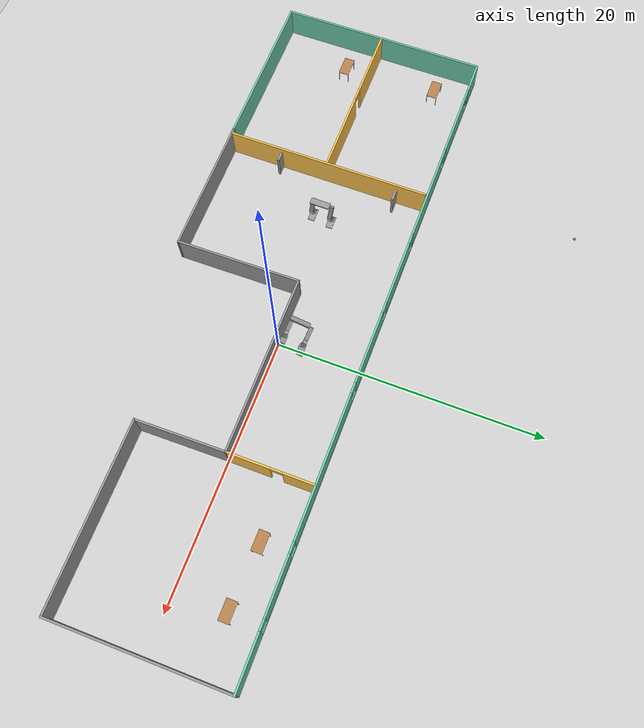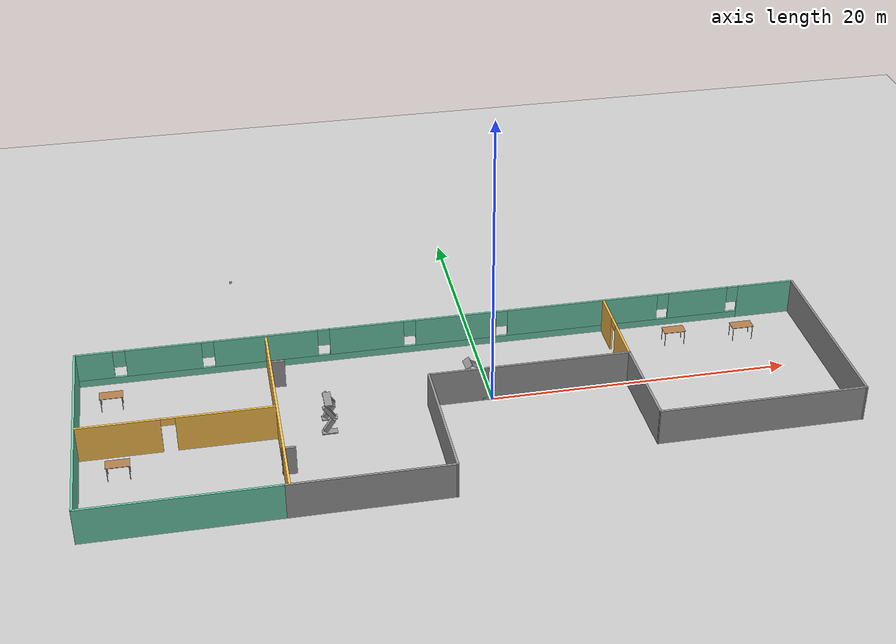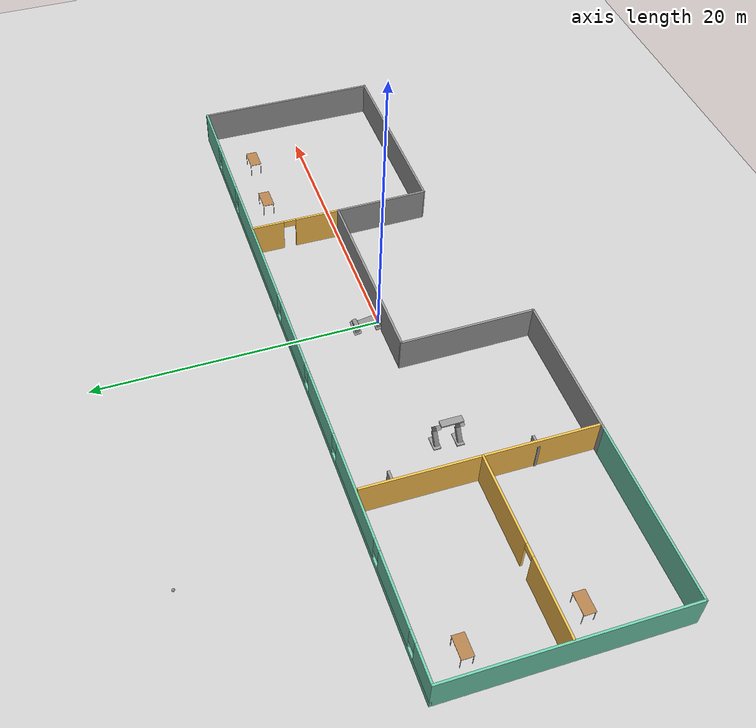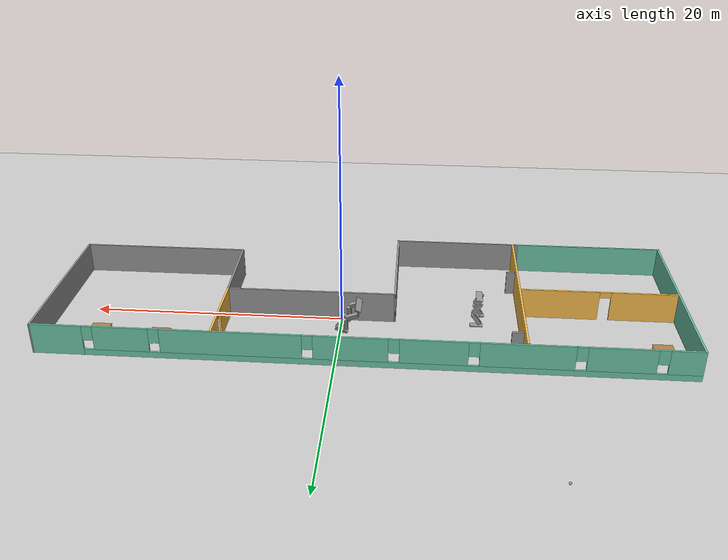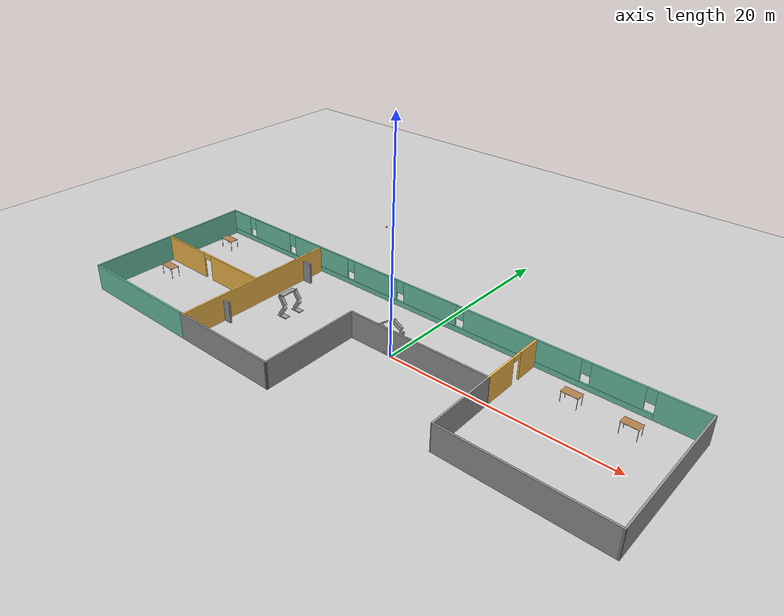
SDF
<sdf version="1.6">
 <world name="default">
  <plugin name="welcome_message" filename="libwelcome_message.so"/>
  <light name="sun" type="directional">
   <pose>0 0 10 0 -0 0</pose>
   <diffuse>0.8 0.8 0.8 1</diffuse>
   <specular>0.2 0.2 0.2 1</specular>
   <attenuation>
    <range>1000</range>
    <constant>0.9</constant>
    <linear>0.01</linear>
    <quadratic>0.001</quadratic>
   </attenuation>
   <direction>-0.5 0.1 -0.9</direction>
  </light>
  <model name="ground_plane">
   <static>1</static>
   <link name="link">
    <collision name="collision">
     <geometry><plane><normal>0 0 1</normal><size>100 100</size></plane></geometry>
     <surface>
      <contact><collide_bitmask>65535</collide_bitmask></contact>
      <friction><ode><mu>100</mu><mu2>50</mu2></ode></friction>
     </surface>
    </collision>
    <visual name="visual">
     <cast_shadows>0</cast_shadows>
     <geometry><plane><normal>0 0 1</normal><size>100 100</size></plane></geometry>
     <material>
      <script><uri>file://media/materials/scripts/gazebo.material</uri><name>Gazebo/Grey</name></script>
     </material>
    </visual>
   </link>
  </model>
  <gravity>0 0 -9.8</gravity>
  <magnetic_field>6e-06 2.3e-05 -4.2e-05</magnetic_field>
  <atmosphere type="adiabatic"/>
  <physics name="default_physics" default="0" type="ode">
   <max_step_size>0.001</max_step_size>
   <real_time_factor>1</real_time_factor>
   <real_time_update_rate>1000</real_time_update_rate>
  </physics>
  <scene><ambient>0.4 0.4 0.4 1</ambient><background>0.7 0.7 0.7 1</background><shadows>1</shadows></scene>
  <spherical_coordinates>
   <surface_model>EARTH_WGS84</surface_model>
   <latitude_deg>0</latitude_deg>
   <longitude_deg>0</longitude_deg>
   <elevation>0</elevation>
   <heading_deg>0</heading_deg>
  </spherical_coordinates>
  <model name="Humanoid">
   <link name="link_0">
    <pose>-0.048492 0.285713 -0.132344 0 -0 0</pose>
    <inertial>
     <mass>1</mass>
     <inertia>
      <ixx>0.166667</ixx>
      <ixy>0</ixy>
      <ixz>0</ixz>
      <iyy>0.166667</iyy>
      <iyz>0</iyz>
      <izz>0.166667</izz>
     </inertia>
    </inertial>
    <visual name="visual">
     <geometry><box><size>1 0.5 0.3</size></box></geometry>
     <material>
      <lighting>1</lighting>
      <script><uri>file://media/materials/scripts/gazebo.material</uri><name>Gazebo/Grey</name></script>
      <shader type="pixel"><normal_map>__default__</normal_map></shader>
      <ambient>0.3 0.3 0.3 1</ambient>
      <diffuse>0.7 0.7 0.7 1</diffuse>
      <specular>0.01 0.01 0.01 1</specular>
      <emissive>0 0 0 1</emissive>
     </material>
    </visual>
    <collision name="collision">
     <geometry><box><size>1 0.5 0.3</size></box></geometry>
     <surface>
      <friction>
       <ode><mu>1</mu><mu2>1</mu2><fdir1>0 0 0</fdir1><slip1>0</slip1><slip2>0</slip2></ode>
       <torsional>
        <coefficient>1</coefficient>
        <patch_radius>0</patch_radius>
        <surface_radius>0</surface_radius>
        <use_patch_radius>1</use_patch_radius>
        <ode><slip>0</slip></ode>
       </torsional>
      </friction>
      <bounce><restitution_coefficient>0</restitution_coefficient><threshold>1e+06</threshold></bounce>
      <contact>
       <collide_without_contact>0</collide_without_contact>
       <collide_without_contact_bitmask>1</collide_without_contact_bitmask>
       <collide_bitmask>1</collide_bitmask>
       <ode>
        <soft_cfm>0</soft_cfm>
        <soft_erp>0.2</soft_erp>
        <kp>1e+13</kp>
        <kd>1</kd>
        <max_vel>0.01</max_vel>
        <min_depth>0</min_depth>
       </ode>
       <bullet>
        <split_impulse>1</split_impulse>
        <split_impulse_penetration_threshold>-0.01</split_impulse_penetration_threshold>
        <soft_cfm>0</soft_cfm>
        <soft_erp>0.2</soft_erp>
        <kp>1e+13</kp>
        <kd>1</kd>
       </bullet>
      </contact>
     </surface>
    </collision>
   </link>
   <link name="link_0_clone">
    <pose>0.107629 1.78606 -0.132344 0 -0 0</pose>
    <inertial>
     <mass>1</mass>
     <inertia>
      <ixx>0.166667</ixx>
      <ixy>0</ixy>
      <ixz>0</ixz>
      <iyy>0.166667</iyy>
      <iyz>0</iyz>
      <izz>0.166667</izz>
     </inertia>
    </inertial>
    <visual name="visual">
     <geometry><box><size>1 0.5 0.3</size></box></geometry>
     <material>
      <lighting>1</lighting>
      <script><uri>file://media/materials/scripts/gazebo.material</uri><name>Gazebo/Grey</name></script>
      <shader type="pixel"><normal_map>__default__</normal_map></shader>
      <ambient>0.3 0.3 0.3 1</ambient>
      <diffuse>0.7 0.7 0.7 1</diffuse>
      <specular>0.01 0.01 0.01 1</specular>
      <emissive>0 0 0 1</emissive>
     </material>
    </visual>
    <collision name="collision">
     <geometry><box><size>1 0.5 0.3</size></box></geometry>
     <surface>
      <friction>
       <ode><mu>1</mu><mu2>1</mu2><fdir1>0 0 0</fdir1><slip1>0</slip1><slip2>0</slip2></ode>
       <torsional>
        <coefficient>1</coefficient>
        <patch_radius>0</patch_radius>
        <surface_radius>0</surface_radius>
        <use_patch_radius>1</use_patch_radius>
        <ode><slip>0</slip></ode>
       </torsional>
      </friction>
      <bounce><restitution_coefficient>0</restitution_coefficient><threshold>1e+06</threshold></bounce>
      <contact>
       <collide_without_contact>0</collide_without_contact>
       <collide_without_contact_bitmask>1</collide_without_contact_bitmask>
       <collide_bitmask>1</collide_bitmask>
       <ode>
        <soft_cfm>0</soft_cfm>
        <soft_erp>0.2</soft_erp>
        <kp>1e+13</kp>
        <kd>1</kd>
        <max_vel>0.01</max_vel>
        <min_depth>0</min_depth>
       </ode>
       <bullet>
        <split_impulse>1</split_impulse>
        <split_impulse_penetration_threshold>-0.01</split_impulse_penetration_threshold>
        <soft_cfm>0</soft_cfm>
        <soft_erp>0.2</soft_erp>
        <kp>1e+13</kp>
        <kd>1</kd>
       </bullet>
      </contact>
     </surface>
    </collision>
   </link>
   <link name="link_1">
    <pose>-0.048492 0.285713 0.51502 0 0.6 0</pose>
    <inertial>
     <mass>1</mass>
     <inertia>
      <ixx>0.166667</ixx>
      <ixy>0</ixy>
      <ixz>0</ixz>
      <iyy>0.166667</iyy>
      <iyz>0</iyz>
      <izz>0.166667</izz>
     </inertia>
    </inertial>
    <visual name="visual">
     <geometry><box><size>0.3 0.3 1</size></box></geometry>
     <material>
      <lighting>1</lighting>
      <script><uri>file://media/materials/scripts/gazebo.material</uri><name>Gazebo/Grey</name></script>
      <shader type="pixel"><normal_map>__default__</normal_map></shader>
      <ambient>0.3 0.3 0.3 1</ambient>
      <diffuse>0.7 0.7 0.7 1</diffuse>
      <specular>0.01 0.01 0.01 1</specular>
      <emissive>0 0 0 1</emissive>
     </material>
    </visual>
    <collision name="collision">
     <geometry><box><size>0.3 0.3 1</size></box></geometry>
     <surface>
      <friction>
       <ode><mu>1</mu><mu2>1</mu2><fdir1>0 0 0</fdir1><slip1>0</slip1><slip2>0</slip2></ode>
       <torsional>
        <coefficient>1</coefficient>
        <patch_radius>0</patch_radius>
        <surface_radius>0</surface_radius>
        <use_patch_radius>1</use_patch_radius>
        <ode><slip>0</slip></ode>
       </torsional>
      </friction>
      <bounce><restitution_coefficient>0</restitution_coefficient><threshold>1e+06</threshold></bounce>
      <contact>
       <collide_without_contact>0</collide_without_contact>
       <collide_without_contact_bitmask>1</collide_without_contact_bitmask>
       <collide_bitmask>1</collide_bitmask>
       <ode>
        <soft_cfm>0</soft_cfm>
        <soft_erp>0.2</soft_erp>
        <kp>1e+13</kp>
        <kd>1</kd>
        <max_vel>0.01</max_vel>
        <min_depth>0</min_depth>
       </ode>
       <bullet>
        <split_impulse>1</split_impulse>
        <split_impulse_penetration_threshold>-0.01</split_impulse_penetration_threshold>
        <soft_cfm>0</soft_cfm>
        <soft_erp>0.2</soft_erp>
        <kp>1e+13</kp>
        <kd>1</kd>
       </bullet>
      </contact>
     </surface>
    </collision>
   </link>
   <link name="link_1_clone">
    <pose>-0.048492 0.285713 1.50975 0 -0.6 0</pose>
    <inertial>
     <mass>1</mass>
     <inertia>
      <ixx>0.166667</ixx>
      <ixy>0</ixy>
      <ixz>0</ixz>
      <iyy>0.166667</iyy>
      <iyz>0</iyz>
      <izz>0.166667</izz>
     </inertia>
    </inertial>
    <visual name="visual">
     <geometry><box><size>0.3 0.3 1</size></box></geometry>
     <material>
      <lighting>1</lighting>
      <script><uri>file://media/materials/scripts/gazebo.material</uri><name>Gazebo/Grey</name></script>
      <shader type="pixel"><normal_map>__default__</normal_map></shader>
      <ambient>0.3 0.3 0.3 1</ambient>
      <diffuse>0.7 0.7 0.7 1</diffuse>
      <specular>0.01 0.01 0.01 1</specular>
      <emissive>0 0 0 1</emissive>
     </material>
    </visual>
    <collision name="collision">
     <geometry><box><size>0.3 0.3 1</size></box></geometry>
     <surface>
      <friction>
       <ode><mu>1</mu><mu2>1</mu2><fdir1>0 0 0</fdir1><slip1>0</slip1><slip2>0</slip2></ode>
       <torsional>
        <coefficient>1</coefficient>
        <patch_radius>0</patch_radius>
        <surface_radius>0</surface_radius>
        <use_patch_radius>1</use_patch_radius>
        <ode><slip>0</slip></ode>
       </torsional>
      </friction>
      <bounce><restitution_coefficient>0</restitution_coefficient><threshold>1e+06</threshold></bounce>
      <contact>
       <collide_without_contact>0</collide_without_contact>
       <collide_without_contact_bitmask>1</collide_without_contact_bitmask>
       <collide_bitmask>1</collide_bitmask>
       <ode>
        <soft_cfm>0</soft_cfm>
        <soft_erp>0.2</soft_erp>
        <kp>1e+13</kp>
        <kd>1</kd>
        <max_vel>0.01</max_vel>
        <min_depth>0</min_depth>
       </ode>
       <bullet>
        <split_impulse>1</split_impulse>
        <split_impulse_penetration_threshold>-0.01</split_impulse_penetration_threshold>
        <soft_cfm>0</soft_cfm>
        <soft_erp>0.2</soft_erp>
        <kp>1e+13</kp>
        <kd>1</kd>
       </bullet>
      </contact>
     </surface>
    </collision>
   </link>
   <link name="link_1_clone_0">
    <pose>0.107629 1.78606 0.51502 0 0.6 0</pose>
    <inertial>
     <mass>1</mass>
     <inertia>
      <ixx>0.166667</ixx>
      <ixy>0</ixy>
      <ixz>0</ixz>
      <iyy>0.166667</iyy>
      <iyz>0</iyz>
      <izz>0.166667</izz>
     </inertia>
    </inertial>
    <visual name="visual">
     <geometry><box><size>0.3 0.3 1</size></box></geometry>
     <material>
      <lighting>1</lighting>
      <script><uri>file://media/materials/scripts/gazebo.material</uri><name>Gazebo/Grey</name></script>
      <shader type="pixel"><normal_map>__default__</normal_map></shader>
      <ambient>0.3 0.3 0.3 1</ambient>
      <diffuse>0.7 0.7 0.7 1</diffuse>
      <specular>0.01 0.01 0.01 1</specular>
      <emissive>0 0 0 1</emissive>
     </material>
    </visual>
    <collision name="collision">
     <geometry><box><size>0.3 0.3 1</size></box></geometry>
     <surface>
      <friction>
       <ode><mu>1</mu><mu2>1</mu2><fdir1>0 0 0</fdir1><slip1>0</slip1><slip2>0</slip2></ode>
       <torsional>
        <coefficient>1</coefficient>
        <patch_radius>0</patch_radius>
        <surface_radius>0</surface_radius>
        <use_patch_radius>1</use_patch_radius>
        <ode><slip>0</slip></ode>
       </torsional>
      </friction>
      <bounce><restitution_coefficient>0</restitution_coefficient><threshold>1e+06</threshold></bounce>
      <contact>
       <collide_without_contact>0</collide_without_contact>
       <collide_without_contact_bitmask>1</collide_without_contact_bitmask>
       <collide_bitmask>1</collide_bitmask>
       <ode>
        <soft_cfm>0</soft_cfm>
        <soft_erp>0.2</soft_erp>
        <kp>1e+13</kp>
        <kd>1</kd>
        <max_vel>0.01</max_vel>
        <min_depth>0</min_depth>
       </ode>
       <bullet>
        <split_impulse>1</split_impulse>
        <split_impulse_penetration_threshold>-0.01</split_impulse_penetration_threshold>
        <soft_cfm>0</soft_cfm>
        <soft_erp>0.2</soft_erp>
        <kp>1e+13</kp>
        <kd>1</kd>
       </bullet>
      </contact>
     </surface>
    </collision>
   </link>
   <link name="link_1_clone_clone">
    <pose>0.107629 1.78606 1.50975 0 -0.6 0</pose>
    <inertial>
     <mass>1</mass>
     <inertia>
      <ixx>0.166667</ixx>
      <ixy>0</ixy>
      <ixz>0</ixz>
      <iyy>0.166667</iyy>
      <iyz>0</iyz>
      <izz>0.166667</izz>
     </inertia>
    </inertial>
    <visual name="visual">
     <geometry><box><size>0.3 0.3 1</size></box></geometry>
     <material>
      <lighting>1</lighting>
      <script><uri>file://media/materials/scripts/gazebo.material</uri><name>Gazebo/Grey</name></script>
      <shader type="pixel"><normal_map>__default__</normal_map></shader>
      <ambient>0.3 0.3 0.3 1</ambient>
      <diffuse>0.7 0.7 0.7 1</diffuse>
      <specular>0.01 0.01 0.01 1</specular>
      <emissive>0 0 0 1</emissive>
     </material>
    </visual>
    <collision name="collision">
     <geometry><box><size>0.3 0.3 1</size></box></geometry>
     <surface>
      <friction>
       <ode><mu>1</mu><mu2>1</mu2><fdir1>0 0 0</fdir1><slip1>0</slip1><slip2>0</slip2></ode>
       <torsional>
        <coefficient>1</coefficient>
        <patch_radius>0</patch_radius>
        <surface_radius>0</surface_radius>
        <use_patch_radius>1</use_patch_radius>
        <ode><slip>0</slip></ode>
       </torsional>
      </friction>
      <bounce><restitution_coefficient>0</restitution_coefficient><threshold>1e+06</threshold></bounce>
      <contact>
       <collide_without_contact>0</collide_without_contact>
       <collide_without_contact_bitmask>1</collide_without_contact_bitmask>
       <collide_bitmask>1</collide_bitmask>
       <ode>
        <soft_cfm>0</soft_cfm>
        <soft_erp>0.2</soft_erp>
        <kp>1e+13</kp>
        <kd>1</kd>
        <max_vel>0.01</max_vel>
        <min_depth>0</min_depth>
       </ode>
       <bullet>
        <split_impulse>1</split_impulse>
        <split_impulse_penetration_threshold>-0.01</split_impulse_penetration_threshold>
        <soft_cfm>0</soft_cfm>
        <soft_erp>0.2</soft_erp>
        <kp>1e+13</kp>
        <kd>1</kd>
       </bullet>
      </contact>
     </surface>
    </collision>
   </link>
   <link name="link_2">
    <pose>-0.048492 0.885713 2.05711 0 -0 0</pose>
    <inertial>
     <mass>1</mass>
     <inertia>
      <ixx>0.166667</ixx>
      <ixy>0</ixy>
      <ixz>0</ixz>
      <iyy>0.166667</iyy>
      <iyz>0</iyz>
      <izz>0.166667</izz>
     </inertia>
    </inertial>
    <visual name="visual">
     <geometry><box><size>0.5 1.5 0.1</size></box></geometry>
     <material>
      <lighting>1</lighting>
      <script><uri>file://media/materials/scripts/gazebo.material</uri><name>Gazebo/Grey</name></script>
      <shader type="pixel"><normal_map>__default__</normal_map></shader>
      <ambient>0.3 0.3 0.3 1</ambient>
      <diffuse>0.7 0.7 0.7 1</diffuse>
      <specular>0.01 0.01 0.01 1</specular>
      <emissive>0 0 0 1</emissive>
     </material>
    </visual>
    <collision name="collision">
     <geometry><box><size>0.5 1.5 0.1</size></box></geometry>
     <surface>
      <friction>
       <ode><mu>1</mu><mu2>1</mu2><fdir1>0 0 0</fdir1><slip1>0</slip1><slip2>0</slip2></ode>
       <torsional>
        <coefficient>1</coefficient>
        <patch_radius>0</patch_radius>
        <surface_radius>0</surface_radius>
        <use_patch_radius>1</use_patch_radius>
        <ode><slip>0</slip></ode>
       </torsional>
      </friction>
      <bounce><restitution_coefficient>0</restitution_coefficient><threshold>1e+06</threshold></bounce>
      <contact>
       <collide_without_contact>0</collide_without_contact>
       <collide_without_contact_bitmask>1</collide_without_contact_bitmask>
       <collide_bitmask>1</collide_bitmask>
       <ode>
        <soft_cfm>0</soft_cfm>
        <soft_erp>0.2</soft_erp>
        <kp>1e+13</kp>
        <kd>1</kd>
        <max_vel>0.01</max_vel>
        <min_depth>0</min_depth>
       </ode>
       <bullet>
        <split_impulse>1</split_impulse>
        <split_impulse_penetration_threshold>-0.01</split_impulse_penetration_threshold>
        <soft_cfm>0</soft_cfm>
        <soft_erp>0.2</soft_erp>
        <kp>1e+13</kp>
        <kd>1</kd>
       </bullet>
      </contact>
     </surface>
    </collision>
   </link>
   <joint name="link_1_JOINT_9" type="revolute">
    <parent>link_1</parent>
    <child>link_0</child>
    <axis>
     <xyz>1 0 0</xyz>
     <use_parent_model_frame>0</use_parent_model_frame>
     <limit>
      <lower>-1.79769e+308</lower>
      <upper>1.79769e+308</upper>
      <effort>-1</effort>
      <velocity>-1</velocity>
     </limit>
     <dynamics>
      <spring_reference>0</spring_reference>
      <spring_stiffness>0</spring_stiffness>
      <damping>0</damping>
      <friction>0</friction>
     </dynamics>
    </axis>
    <physics>
     <ode><limit><cfm>0</cfm><erp>0.2</erp></limit><suspension><cfm>0</cfm><erp>0.2</erp></suspension></ode>
    </physics>
   </joint>
   <joint name="link_1_clone_0_JOINT_10" type="revolute">
    <parent>link_1_clone_0</parent>
    <child>link_0_clone</child>
    <axis>
     <xyz>1 0 0</xyz>
     <use_parent_model_frame>0</use_parent_model_frame>
     <limit>
      <lower>-1.79769e+308</lower>
      <upper>1.79769e+308</upper>
      <effort>-1</effort>
      <velocity>-1</velocity>
     </limit>
     <dynamics>
      <spring_reference>0</spring_reference>
      <spring_stiffness>0</spring_stiffness>
      <damping>0</damping>
      <friction>0</friction>
     </dynamics>
    </axis>
    <physics>
     <ode><limit><cfm>0</cfm><erp>0.2</erp></limit><suspension><cfm>0</cfm><erp>0.2</erp></suspension></ode>
    </physics>
   </joint>
   <joint name="link_1_clone_JOINT_7" type="revolute">
    <parent>link_1_clone</parent>
    <child>link_1</child>
    <axis>
     <xyz>1 0 0</xyz>
     <use_parent_model_frame>0</use_parent_model_frame>
     <limit>
      <lower>-1.79769e+308</lower>
      <upper>1.79769e+308</upper>
      <effort>-1</effort>
      <velocity>-1</velocity>
     </limit>
     <dynamics>
      <spring_reference>0</spring_reference>
      <spring_stiffness>0</spring_stiffness>
      <damping>0</damping>
      <friction>0</friction>
     </dynamics>
    </axis>
    <physics>
     <ode><limit><cfm>0</cfm><erp>0.2</erp></limit><suspension><cfm>0</cfm><erp>0.2</erp></suspension></ode>
    </physics>
   </joint>
   <joint name="link_1_clone_clone_JOINT_8" type="revolute">
    <parent>link_1_clone_clone</parent>
    <child>link_1_clone_0</child>
    <axis>
     <xyz>1 0 0</xyz>
     <use_parent_model_frame>0</use_parent_model_frame>
     <limit>
      <lower>-1.79769e+308</lower>
      <upper>1.79769e+308</upper>
      <effort>-1</effort>
      <velocity>-1</velocity>
     </limit>
     <dynamics>
      <spring_reference>0</spring_reference>
      <spring_stiffness>0</spring_stiffness>
      <damping>0</damping>
      <friction>0</friction>
     </dynamics>
    </axis>
    <physics>
     <ode><limit><cfm>0</cfm><erp>0.2</erp></limit><suspension><cfm>0</cfm><erp>0.2</erp></suspension></ode>
    </physics>
   </joint>
   <joint name="link_2_JOINT_5" type="revolute">
    <parent>link_2</parent>
    <child>link_1_clone</child>
    <axis>
     <xyz>1 0 0</xyz>
     <use_parent_model_frame>0</use_parent_model_frame>
     <limit>
      <lower>-1.79769e+308</lower>
      <upper>1.79769e+308</upper>
      <effort>-1</effort>
      <velocity>-1</velocity>
     </limit>
     <dynamics>
      <spring_reference>0</spring_reference>
      <spring_stiffness>0</spring_stiffness>
      <damping>0</damping>
      <friction>0</friction>
     </dynamics>
    </axis>
    <physics>
     <ode><limit><cfm>0</cfm><erp>0.2</erp></limit><suspension><cfm>0</cfm><erp>0.2</erp></suspension></ode>
    </physics>
   </joint>
   <joint name="link_2_JOINT_6" type="revolute">
    <parent>link_2</parent>
    <child>link_1_clone_clone</child>
    <axis>
     <xyz>1 0 0</xyz>
     <use_parent_model_frame>0</use_parent_model_frame>
     <limit>
      <lower>-1.79769e+308</lower>
      <upper>1.79769e+308</upper>
      <effort>-1</effort>
      <velocity>-1</velocity>
     </limit>
     <dynamics>
      <spring_reference>0</spring_reference>
      <spring_stiffness>0</spring_stiffness>
      <damping>0</damping>
      <friction>0</friction>
     </dynamics>
    </axis>
    <physics>
     <ode><limit><cfm>0</cfm><erp>0.2</erp></limit><suspension><cfm>0</cfm><erp>0.2</erp></suspension></ode>
    </physics>
   </joint>
   <static>1</static>
   <pose>-0.317711 -0.030167 0.63133 -0.239963 -0.538351 0.109355</pose>
  </model>
  <model name="MyBuilding">
   <pose>-1.8548 -1.4802 2e-06 0.0085 -0 0</pose>
   <link name="Door_4">
    <collision name="Door_4_Collision">
     <geometry><box><size>0.9 0.17 2</size></box></geometry>
     <pose>0 0 1 0 -0 0</pose>
    </collision>
    <visual name="Door_4_Visual">
     <pose>0 0 1 0 -0 0</pose>
     <geometry><box><size>0.9 0.17 2</size></box></geometry>
     <material>
      <script><uri>file://media/materials/scripts/gazebo.material</uri><name>Gazebo/Grey</name></script>
     </material>
    </visual>
    <pose>-11.699 5.51769 0 0 -0 0</pose>
   </link>
   <link name="Door_5">
    <collision name="Door_5_Collision">
     <geometry><box><size>0.9 0.17 2</size></box></geometry>
     <pose>0 0 1 0 -0 0</pose>
    </collision>
    <visual name="Door_5_Visual">
     <pose>0 0 1 0 -0 0</pose>
     <geometry><box><size>0.9 0.17 2</size></box></geometry>
     <material>
      <script><uri>file://media/materials/scripts/gazebo.material</uri><name>Gazebo/Grey</name></script>
     </material>
    </visual>
    <pose>-11.913 -3.79174 0 0 -0 0</pose>
   </link>
   <link name="Wall_22">
    <collision name="Wall_22_Collision">
     <geometry><box><size>16 0.15 2.5</size></box></geometry>
     <pose>0 0 1.25 0 -0 0</pose>
    </collision>
    <visual name="Wall_22_Visual">
     <pose>0 0 1.25 0 -0 0</pose>
     <geometry><box><size>16 0.15 2.5</size></box></geometry>
     <material>
      <script><uri>file://media/materials/scripts/gazebo.material</uri><name>Gazebo/Grey</name></script>
      <ambient>0.435294 0.796078 0.67451 1</ambient>
     </material>
     <meta><layer>0</layer></meta>
    </visual>
    <pose>-24.7002 0.000204 0 0 0 -1.5708</pose>
   </link>
   <link name="Wall_23">
    <collision name="Wall_23_Collision">
     <geometry><box><size>12.25 0.15 2.5</size></box></geometry>
     <pose>0 0 1.25 0 -0 0</pose>
    </collision>
    <visual name="Wall_23_Visual">
     <pose>0 0 1.25 0 -0 0</pose>
     <geometry><box><size>12.25 0.15 2.5</size></box></geometry>
     <material>
      <script><uri>file://media/materials/scripts/gazebo.material</uri><name>Gazebo/Grey</name></script>
      <ambient>0.435294 0.796078 0.67451 1</ambient>
     </material>
     <meta><layer>0</layer></meta>
    </visual>
    <pose>-18.6502 -7.9248 0 0 -0 0</pose>
   </link>
   <link name="Wall_24">
    <collision name="Wall_24_Collision">
     <geometry><box><size>10.5 0.15 2.5</size></box></geometry>
     <pose>0 0 1.25 0 -0 0</pose>
    </collision>
    <visual name="Wall_24_Visual">
     <pose>0 0 1.25 0 -0 0</pose>
     <geometry><box><size>10.5 0.15 2.5</size></box></geometry>
     <material>
      <script><uri>file://media/materials/scripts/gazebo.material</uri><name>Gazebo/Grey</name></script>
      <ambient>1 1 1 1</ambient>
     </material>
     <meta><layer>0</layer></meta>
    </visual>
    <pose>-7.42514 -7.92474 0 0 -0 1e-05</pose>
   </link>
   <link name="Wall_25">
    <collision name="Wall_25_Collision">
     <geometry><box><size>9.55411 0.15 2.5</size></box></geometry>
     <pose>0 0 1.25 0 -0 0</pose>
    </collision>
    <visual name="Wall_25_Visual">
     <pose>0 0 1.25 0 -0 0</pose>
     <geometry><box><size>9.55411 0.15 2.5</size></box></geometry>
     <material>
      <script><uri>file://media/materials/scripts/gazebo.material</uri><name>Gazebo/Grey</name></script>
      <ambient>1 1 1 1</ambient>
     </material>
     <meta><layer>0</layer></meta>
    </visual>
    <pose>-2.30359 -3.22294 0 0 -0 1.58218</pose>
   </link>
   <link name="Wall_26">
    <collision name="Wall_26_Collision">
     <geometry><box><size>13.4464 0.15 2.5</size></box></geometry>
     <pose>0 0 1.25 0 -0 0</pose>
    </collision>
    <visual name="Wall_26_Visual">
     <pose>0 0 1.25 0 -0 0</pose>
     <geometry><box><size>13.4464 0.15 2.5</size></box></geometry>
     <material>
      <script><uri>file://media/materials/scripts/gazebo.material</uri><name>Gazebo/Grey</name></script>
      <ambient>1 1 1 1</ambient>
     </material>
     <meta><layer>0</layer></meta>
    </visual>
    <pose>4.34461 1.47901 0 0 -0 3e-05</pose>
   </link>
   <link name="Wall_27">
    <collision name="Wall_27_Collision">
     <geometry><box><size>6.80436 0.15 2.5</size></box></geometry>
     <pose>0 0 1.25 0 -0 0</pose>
    </collision>
    <visual name="Wall_27_Visual">
     <pose>0 0 1.25 0 -0 0</pose>
     <geometry><box><size>6.80436 0.15 2.5</size></box></geometry>
     <material>
      <script><uri>file://media/materials/scripts/gazebo.material</uri><name>Gazebo/Grey</name></script>
      <ambient>1 1 1 1</ambient>
     </material>
     <meta><layer>0</layer></meta>
    </visual>
    <pose>11.0464 -1.84774 0 0 0 -1.5547</pose>
   </link>
   <link name="Wall_28">
    <collision name="Wall_28_Collision">
     <geometry><box><size>13.75 0.15 2.5</size></box></geometry>
     <pose>0 0 1.25 0 -0 0</pose>
    </collision>
    <visual name="Wall_28_Visual">
     <pose>0 0 1.25 0 -0 0</pose>
     <geometry><box><size>13.75 0.15 2.5</size></box></geometry>
     <material>
      <script><uri>file://media/materials/scripts/gazebo.material</uri><name>Gazebo/Grey</name></script>
      <ambient>1 1 1 1</ambient>
     </material>
     <meta><layer>0</layer></meta>
    </visual>
    <pose>17.8999 -5.17469 0 0 -0 0</pose>
   </link>
   <link name="Wall_29">
    <collision name="Wall_29_Collision">
     <geometry><box><size>13.2501 0.15 2.5</size></box></geometry>
     <pose>0 0 1.25 0 -0 0</pose>
    </collision>
    <visual name="Wall_29_Visual">
     <pose>0 0 1.25 0 -0 0</pose>
     <geometry><box><size>13.2501 0.15 2.5</size></box></geometry>
     <material>
      <script><uri>file://media/materials/scripts/gazebo.material</uri><name>Gazebo/Grey</name></script>
      <ambient>1 1 1 1</ambient>
     </material>
     <meta><layer>0</layer></meta>
    </visual>
    <pose>24.6749 1.37526 0 0 -0 1.57462</pose>
   </link>
   <link name="Wall_30">
    <pose>-0.025193 7.9252 0 0 -0 3.14159</pose>
    <visual name="Wall_30_Visual_0">
     <pose>-22.7354 0 1.25 0 -0 0</pose>
     <geometry><box><size>4.0293 0.15 2.5</size></box></geometry>
     <material>
      <script><uri>file://media/materials/scripts/gazebo.material</uri><name>Gazebo/Grey</name></script>
      <ambient>0.435294 0.796078 0.67451 1</ambient>
     </material>
     <meta><layer>0</layer></meta>
    </visual>
    <collision name="Wall_30_Collision_0">
     <geometry><box><size>4.0293 0.15 2.5</size></box></geometry>
     <pose>-22.7354 0 1.25 0 -0 0</pose>
    </collision>
    <visual name="Wall_30_Visual_1">
     <pose>2.01465 0 0.25 0 -0 0</pose>
     <geometry><box><size>45.4707 0.15 0.5</size></box></geometry>
     <material>
      <script><uri>file://media/materials/scripts/gazebo.material</uri><name>Gazebo/Grey</name></script>
      <ambient>0.435294 0.796078 0.67451 1</ambient>
     </material>
     <meta><layer>0</layer></meta>
    </visual>
    <collision name="Wall_30_Collision_1">
     <geometry><box><size>45.4707 0.15 0.5</size></box></geometry>
     <pose>2.01465 0 0.25 0 -0 0</pose>
    </collision>
    <visual name="Wall_30_Visual_2">
     <pose>-17.8061 0 1.5 0 -0 0</pose>
     <geometry><box><size>4.22924 0.15 2</size></box></geometry>
     <material>
      <script><uri>file://media/materials/scripts/gazebo.material</uri><name>Gazebo/Grey</name></script>
      <ambient>0.435294 0.796078 0.67451 1</ambient>
     </material>
     <meta><layer>0</layer></meta>
    </visual>
    <collision name="Wall_30_Collision_2">
     <geometry><box><size>4.22924 0.15 2</size></box></geometry>
     <pose>-17.8061 0 1.5 0 -0 0</pose>
    </collision>
    <visual name="Wall_30_Visual_3">
     <pose>-9.5667 0 1.5 0 -0 0</pose>
     <geometry><box><size>10.6495 0.15 2</size></box></geometry>
     <material>
      <script><uri>file://media/materials/scripts/gazebo.material</uri><name>Gazebo/Grey</name></script>
      <ambient>0.435294 0.796078 0.67451 1</ambient>
     </material>
     <meta><layer>0</layer></meta>
    </visual>
    <collision name="Wall_30_Collision_3">
     <geometry><box><size>10.6495 0.15 2</size></box></geometry>
     <pose>-9.5667 0 1.5 0 -0 0</pose>
    </collision>
    <visual name="Wall_30_Visual_4">
     <pose>-0.658536 0 1.5 0 -0 0</pose>
     <geometry><box><size>5.5668 0.15 2</size></box></geometry>
     <material>
      <script><uri>file://media/materials/scripts/gazebo.material</uri><name>Gazebo/Grey</name></script>
      <ambient>0.435294 0.796078 0.67451 1</ambient>
     </material>
     <meta><layer>0</layer></meta>
    </visual>
    <collision name="Wall_30_Collision_4">
     <geometry><box><size>5.5668 0.15 2</size></box></geometry>
     <pose>-0.658536 0 1.5 0 -0 0</pose>
    </collision>
    <visual name="Wall_30_Visual_5">
     <pose>5.44075 0 1.5 0 -0 0</pose>
     <geometry><box><size>5.03177 0.15 2</size></box></geometry>
     <material>
      <script><uri>file://media/materials/scripts/gazebo.material</uri><name>Gazebo/Grey</name></script>
      <ambient>0.435294 0.796078 0.67451 1</ambient>
     </material>
     <meta><layer>0</layer></meta>
    </visual>
    <collision name="Wall_30_Collision_5">
     <geometry><box><size>5.03177 0.15 2</size></box></geometry>
     <pose>5.44075 0 1.5 0 -0 0</pose>
    </collision>
    <visual name="Wall_30_Visual_6">
     <pose>12.2088 0 1.5 0 -0 0</pose>
     <geometry><box><size>6.90436 0.15 2</size></box></geometry>
     <material>
      <script><uri>file://media/materials/scripts/gazebo.material</uri><name>Gazebo/Grey</name></script>
      <ambient>0.435294 0.796078 0.67451 1</ambient>
     </material>
     <meta><layer>0</layer></meta>
    </visual>
    <collision name="Wall_30_Collision_6">
     <geometry><box><size>6.90436 0.15 2</size></box></geometry>
     <pose>12.2088 0 1.5 0 -0 0</pose>
    </collision>
    <visual name="Wall_30_Visual_7">
     <pose>18.9501 0 1.5 0 -0 0</pose>
     <geometry><box><size>4.97827 0.15 2</size></box></geometry>
     <material>
      <script><uri>file://media/materials/scripts/gazebo.material</uri><name>Gazebo/Grey</name></script>
      <ambient>0.435294 0.796078 0.67451 1</ambient>
     </material>
     <meta><layer>0</layer></meta>
    </visual>
    <collision name="Wall_30_Collision_7">
     <geometry><box><size>4.97827 0.15 2</size></box></geometry>
     <pose>18.9501 0 1.5 0 -0 0</pose>
    </collision>
    <visual name="Wall_30_Visual_8">
     <pose>23.4946 0 1.5 0 -0 0</pose>
     <geometry><box><size>2.51073 0.15 2</size></box></geometry>
     <material>
      <script><uri>file://media/materials/scripts/gazebo.material</uri><name>Gazebo/Grey</name></script>
      <ambient>0.435294 0.796078 0.67451 1</ambient>
     </material>
     <meta><layer>0</layer></meta>
    </visual>
    <collision name="Wall_30_Collision_8">
     <geometry><box><size>2.51073 0.15 2</size></box></geometry>
     <pose>23.4946 0 1.5 0 -0 0</pose>
    </collision>
    <visual name="Wall_30_Visual_9">
     <pose>-20.3207 0 1.9 0 -0 0</pose>
     <geometry><box><size>0.8 0.15 1.2</size></box></geometry>
     <material>
      <script><uri>file://media/materials/scripts/gazebo.material</uri><name>Gazebo/Grey</name></script>
      <ambient>0.435294 0.796078 0.67451 1</ambient>
     </material>
     <meta><layer>0</layer></meta>
    </visual>
    <collision name="Wall_30_Collision_9">
     <geometry><box><size>0.8 0.15 1.2</size></box></geometry>
     <pose>-20.3207 0 1.9 0 -0 0</pose>
    </collision>
    <visual name="Wall_30_Visual_10">
     <pose>-15.2915 0 1.9 0 -0 0</pose>
     <geometry><box><size>0.8 0.15 1.2</size></box></geometry>
     <material>
      <script><uri>file://media/materials/scripts/gazebo.material</uri><name>Gazebo/Grey</name></script>
      <ambient>0.435294 0.796078 0.67451 1</ambient>
     </material>
     <meta><layer>0</layer></meta>
    </visual>
    <collision name="Wall_30_Collision_10">
     <geometry><box><size>0.8 0.15 1.2</size></box></geometry>
     <pose>-15.2915 0 1.9 0 -0 0</pose>
    </collision>
    <visual name="Wall_30_Visual_11">
     <pose>-3.84193 0 1.9 0 -0 0</pose>
     <geometry><box><size>0.8 0.15 1.2</size></box></geometry>
     <material>
      <script><uri>file://media/materials/scripts/gazebo.material</uri><name>Gazebo/Grey</name></script>
      <ambient>0.435294 0.796078 0.67451 1</ambient>
     </material>
     <meta><layer>0</layer></meta>
    </visual>
    <collision name="Wall_30_Collision_11">
     <geometry><box><size>0.8 0.15 1.2</size></box></geometry>
     <pose>-3.84193 0 1.9 0 -0 0</pose>
    </collision>
    <visual name="Wall_30_Visual_12">
     <pose>2.52486 0 1.9 0 -0 0</pose>
     <geometry><box><size>0.8 0.15 1.2</size></box></geometry>
     <material>
      <script><uri>file://media/materials/scripts/gazebo.material</uri><name>Gazebo/Grey</name></script>
      <ambient>0.435294 0.796078 0.67451 1</ambient>
     </material>
     <meta><layer>0</layer></meta>
    </visual>
    <collision name="Wall_30_Collision_12">
     <geometry><box><size>0.8 0.15 1.2</size></box></geometry>
     <pose>2.52486 0 1.9 0 -0 0</pose>
    </collision>
    <visual name="Wall_30_Visual_13">
     <pose>8.35664 0 1.9 0 -0 0</pose>
     <geometry><box><size>0.8 0.15 1.2</size></box></geometry>
     <material>
      <script><uri>file://media/materials/scripts/gazebo.material</uri><name>Gazebo/Grey</name></script>
      <ambient>0.435294 0.796078 0.67451 1</ambient>
     </material>
     <meta><layer>0</layer></meta>
    </visual>
    <collision name="Wall_30_Collision_13">
     <geometry><box><size>0.8 0.15 1.2</size></box></geometry>
     <pose>8.35664 0 1.9 0 -0 0</pose>
    </collision>
    <visual name="Wall_30_Visual_14">
     <pose>16.061 0 1.9 0 -0 0</pose>
     <geometry><box><size>0.8 0.15 1.2</size></box></geometry>
     <material>
      <script><uri>file://media/materials/scripts/gazebo.material</uri><name>Gazebo/Grey</name></script>
      <ambient>0.435294 0.796078 0.67451 1</ambient>
     </material>
     <meta><layer>0</layer></meta>
    </visual>
    <collision name="Wall_30_Collision_14">
     <geometry><box><size>0.8 0.15 1.2</size></box></geometry>
     <pose>16.061 0 1.9 0 -0 0</pose>
    </collision>
    <visual name="Wall_30_Visual_15">
     <pose>21.8393 0 1.9 0 -0 0</pose>
     <geometry><box><size>0.8 0.15 1.2</size></box></geometry>
     <material>
      <script><uri>file://media/materials/scripts/gazebo.material</uri><name>Gazebo/Grey</name></script>
      <ambient>0.435294 0.796078 0.67451 1</ambient>
     </material>
     <meta><layer>0</layer></meta>
    </visual>
    <collision name="Wall_30_Collision_15">
     <geometry><box><size>0.8 0.15 1.2</size></box></geometry>
     <pose>21.8393 0 1.9 0 -0 0</pose>
    </collision>
   </link>
   <link name="Wall_32">
    <collision name="Wall_32_Collision">
     <geometry><box><size>15.75 0.15 2.5</size></box></geometry>
     <pose>0 0 1.25 0 -0 0</pose>
    </collision>
    <visual name="Wall_32_Visual">
     <pose>0 0 1.25 0 -0 0</pose>
     <geometry><box><size>15.75 0.15 2.5</size></box></geometry>
     <material>
      <script><uri>file://media/materials/scripts/gazebo.material</uri><name>Gazebo/Grey</name></script>
      <ambient>1 0.764706 0.305882 1</ambient>
     </material>
     <meta><layer>0</layer></meta>
    </visual>
    <pose>-12.2342 -0.088796 0 0 0 -1.5708</pose>
   </link>
   <link name="Wall_34">
    <pose>-18.4182 -0.099796 0 0 -0 0</pose>
    <visual name="Wall_34_Visual_0">
     <pose>-3.62857 0 1.25 0 -0 0</pose>
     <geometry><box><size>5.24287 0.15 2.5</size></box></geometry>
     <material>
      <script><uri>file://media/materials/scripts/gazebo.material</uri><name>Gazebo/Grey</name></script>
      <ambient>1 0.764706 0.305882 1</ambient>
     </material>
     <meta><layer>0</layer></meta>
    </visual>
    <collision name="Wall_34_Collision_0">
     <geometry><box><size>5.24287 0.15 2.5</size></box></geometry>
     <pose>-3.62857 0 1.25 0 -0 0</pose>
    </collision>
    <visual name="Wall_34_Visual_1">
     <pose>3.07144 0 1.25 0 -0 0</pose>
     <geometry><box><size>6.35713 0.15 2.5</size></box></geometry>
     <material>
      <script><uri>file://media/materials/scripts/gazebo.material</uri><name>Gazebo/Grey</name></script>
      <ambient>1 0.764706 0.305882 1</ambient>
     </material>
     <meta><layer>0</layer></meta>
    </visual>
    <collision name="Wall_34_Collision_1">
     <geometry><box><size>6.35713 0.15 2.5</size></box></geometry>
     <pose>3.07144 0 1.25 0 -0 0</pose>
    </collision>
    <visual name="Wall_34_Visual_2">
     <pose>-0.557131 0 2.25 0 -0 0</pose>
     <geometry><box><size>0.9 0.15 0.5</size></box></geometry>
     <material>
      <script><uri>file://media/materials/scripts/gazebo.material</uri><name>Gazebo/Grey</name></script>
      <ambient>1 0.764706 0.305882 1</ambient>
     </material>
     <meta><layer>0</layer></meta>
    </visual>
    <collision name="Wall_34_Collision_2">
     <geometry><box><size>0.9 0.15 0.5</size></box></geometry>
     <pose>-0.557131 0 2.25 0 -0 0</pose>
    </collision>
   </link>
   <link name="Wall_36">
    <pose>10.9928 4.6542 0 0 0 -1.5708</pose>
    <visual name="Wall_36_Visual_0">
     <pose>-2.09449 0 1.25 0 -0 0</pose>
     <geometry><box><size>2.31103 0.15 2.5</size></box></geometry>
     <material>
      <script><uri>file://media/materials/scripts/gazebo.material</uri><name>Gazebo/Grey</name></script>
      <ambient>1 0.764706 0.305882 1</ambient>
     </material>
     <meta><layer>0</layer></meta>
    </visual>
    <collision name="Wall_36_Collision_0">
     <geometry><box><size>2.31103 0.15 2.5</size></box></geometry>
     <pose>-2.09449 0 1.25 0 -0 0</pose>
    </collision>
    <visual name="Wall_36_Visual_1">
     <pose>1.60551 0 1.25 0 -0 0</pose>
     <geometry><box><size>3.28897 0.15 2.5</size></box></geometry>
     <material>
      <script><uri>file://media/materials/scripts/gazebo.material</uri><name>Gazebo/Grey</name></script>
      <ambient>1 0.764706 0.305882 1</ambient>
     </material>
     <meta><layer>0</layer></meta>
    </visual>
    <collision name="Wall_36_Collision_1">
     <geometry><box><size>3.28897 0.15 2.5</size></box></geometry>
     <pose>1.60551 0 1.25 0 -0 0</pose>
    </collision>
    <visual name="Wall_36_Visual_2">
     <pose>-0.488973 0 2.25 0 -0 0</pose>
     <geometry><box><size>0.9 0.15 0.5</size></box></geometry>
     <material>
      <script><uri>file://media/materials/scripts/gazebo.material</uri><name>Gazebo/Grey</name></script>
      <ambient>1 0.764706 0.305882 1</ambient>
     </material>
     <meta><layer>0</layer></meta>
    </visual>
    <collision name="Wall_36_Collision_2">
     <geometry><box><size>0.9 0.15 0.5</size></box></geometry>
     <pose>-0.488973 0 2.25 0 -0 0</pose>
    </collision>
   </link>
   <static>1</static>
  </model>
  <model name="Humanoid_0">
   <link name="link_0">
    <pose>-0.048492 0.285713 -0.132344 0 -0 0</pose>
    <inertial>
     <mass>1</mass>
     <inertia>
      <ixx>0.166667</ixx>
      <ixy>0</ixy>
      <ixz>0</ixz>
      <iyy>0.166667</iyy>
      <iyz>0</iyz>
      <izz>0.166667</izz>
     </inertia>
    </inertial>
    <visual name="visual">
     <geometry><box><size>1 0.5 0.3</size></box></geometry>
     <material>
      <lighting>1</lighting>
      <script><uri>file://media/materials/scripts/gazebo.material</uri><name>Gazebo/Grey</name></script>
      <shader type="pixel"><normal_map>__default__</normal_map></shader>
      <ambient>0.3 0.3 0.3 1</ambient>
      <diffuse>0.7 0.7 0.7 1</diffuse>
      <specular>0.01 0.01 0.01 1</specular>
      <emissive>0 0 0 1</emissive>
     </material>
    </visual>
    <collision name="collision">
     <geometry><box><size>1 0.5 0.3</size></box></geometry>
     <surface>
      <friction>
       <ode><mu>1</mu><mu2>1</mu2><fdir1>0 0 0</fdir1><slip1>0</slip1><slip2>0</slip2></ode>
       <torsional>
        <coefficient>1</coefficient>
        <patch_radius>0</patch_radius>
        <surface_radius>0</surface_radius>
        <use_patch_radius>1</use_patch_radius>
        <ode><slip>0</slip></ode>
       </torsional>
      </friction>
      <bounce><restitution_coefficient>0</restitution_coefficient><threshold>1e+06</threshold></bounce>
      <contact>
       <collide_without_contact>0</collide_without_contact>
       <collide_without_contact_bitmask>1</collide_without_contact_bitmask>
       <collide_bitmask>1</collide_bitmask>
       <ode>
        <soft_cfm>0</soft_cfm>
        <soft_erp>0.2</soft_erp>
        <kp>1e+13</kp>
        <kd>1</kd>
        <max_vel>0.01</max_vel>
        <min_depth>0</min_depth>
       </ode>
       <bullet>
        <split_impulse>1</split_impulse>
        <split_impulse_penetration_threshold>-0.01</split_impulse_penetration_threshold>
        <soft_cfm>0</soft_cfm>
        <soft_erp>0.2</soft_erp>
        <kp>1e+13</kp>
        <kd>1</kd>
       </bullet>
      </contact>
     </surface>
    </collision>
   </link>
   <link name="link_0_clone">
    <pose>0.107629 1.78606 -0.132344 0 -0 0</pose>
    <inertial>
     <mass>1</mass>
     <inertia>
      <ixx>0.166667</ixx>
      <ixy>0</ixy>
      <ixz>0</ixz>
      <iyy>0.166667</iyy>
      <iyz>0</iyz>
      <izz>0.166667</izz>
     </inertia>
    </inertial>
    <visual name="visual">
     <geometry><box><size>1 0.5 0.3</size></box></geometry>
     <material>
      <lighting>1</lighting>
      <script><uri>file://media/materials/scripts/gazebo.material</uri><name>Gazebo/Grey</name></script>
      <shader type="pixel"><normal_map>__default__</normal_map></shader>
      <ambient>0.3 0.3 0.3 1</ambient>
      <diffuse>0.7 0.7 0.7 1</diffuse>
      <specular>0.01 0.01 0.01 1</specular>
      <emissive>0 0 0 1</emissive>
     </material>
    </visual>
    <collision name="collision">
     <geometry><box><size>1 0.5 0.3</size></box></geometry>
     <surface>
      <friction>
       <ode><mu>1</mu><mu2>1</mu2><fdir1>0 0 0</fdir1><slip1>0</slip1><slip2>0</slip2></ode>
       <torsional>
        <coefficient>1</coefficient>
        <patch_radius>0</patch_radius>
        <surface_radius>0</surface_radius>
        <use_patch_radius>1</use_patch_radius>
        <ode><slip>0</slip></ode>
       </torsional>
      </friction>
      <bounce><restitution_coefficient>0</restitution_coefficient><threshold>1e+06</threshold></bounce>
      <contact>
       <collide_without_contact>0</collide_without_contact>
       <collide_without_contact_bitmask>1</collide_without_contact_bitmask>
       <collide_bitmask>1</collide_bitmask>
       <ode>
        <soft_cfm>0</soft_cfm>
        <soft_erp>0.2</soft_erp>
        <kp>1e+13</kp>
        <kd>1</kd>
        <max_vel>0.01</max_vel>
        <min_depth>0</min_depth>
       </ode>
       <bullet>
        <split_impulse>1</split_impulse>
        <split_impulse_penetration_threshold>-0.01</split_impulse_penetration_threshold>
        <soft_cfm>0</soft_cfm>
        <soft_erp>0.2</soft_erp>
        <kp>1e+13</kp>
        <kd>1</kd>
       </bullet>
      </contact>
     </surface>
    </collision>
   </link>
   <link name="link_1">
    <pose>-0.048492 0.285713 0.51502 0 0.6 0</pose>
    <inertial>
     <mass>1</mass>
     <inertia>
      <ixx>0.166667</ixx>
      <ixy>0</ixy>
      <ixz>0</ixz>
      <iyy>0.166667</iyy>
      <iyz>0</iyz>
      <izz>0.166667</izz>
     </inertia>
    </inertial>
    <visual name="visual">
     <geometry><box><size>0.3 0.3 1</size></box></geometry>
     <material>
      <lighting>1</lighting>
      <script><uri>file://media/materials/scripts/gazebo.material</uri><name>Gazebo/Grey</name></script>
      <shader type="pixel"><normal_map>__default__</normal_map></shader>
      <ambient>0.3 0.3 0.3 1</ambient>
      <diffuse>0.7 0.7 0.7 1</diffuse>
      <specular>0.01 0.01 0.01 1</specular>
      <emissive>0 0 0 1</emissive>
     </material>
    </visual>
    <collision name="collision">
     <geometry><box><size>0.3 0.3 1</size></box></geometry>
     <surface>
      <friction>
       <ode><mu>1</mu><mu2>1</mu2><fdir1>0 0 0</fdir1><slip1>0</slip1><slip2>0</slip2></ode>
       <torsional>
        <coefficient>1</coefficient>
        <patch_radius>0</patch_radius>
        <surface_radius>0</surface_radius>
        <use_patch_radius>1</use_patch_radius>
        <ode><slip>0</slip></ode>
       </torsional>
      </friction>
      <bounce><restitution_coefficient>0</restitution_coefficient><threshold>1e+06</threshold></bounce>
      <contact>
       <collide_without_contact>0</collide_without_contact>
       <collide_without_contact_bitmask>1</collide_without_contact_bitmask>
       <collide_bitmask>1</collide_bitmask>
       <ode>
        <soft_cfm>0</soft_cfm>
        <soft_erp>0.2</soft_erp>
        <kp>1e+13</kp>
        <kd>1</kd>
        <max_vel>0.01</max_vel>
        <min_depth>0</min_depth>
       </ode>
       <bullet>
        <split_impulse>1</split_impulse>
        <split_impulse_penetration_threshold>-0.01</split_impulse_penetration_threshold>
        <soft_cfm>0</soft_cfm>
        <soft_erp>0.2</soft_erp>
        <kp>1e+13</kp>
        <kd>1</kd>
       </bullet>
      </contact>
     </surface>
    </collision>
   </link>
   <link name="link_1_clone">
    <pose>-0.048492 0.285713 1.50975 0 -0.6 0</pose>
    <inertial>
     <mass>1</mass>
     <inertia>
      <ixx>0.166667</ixx>
      <ixy>0</ixy>
      <ixz>0</ixz>
      <iyy>0.166667</iyy>
      <iyz>0</iyz>
      <izz>0.166667</izz>
     </inertia>
    </inertial>
    <visual name="visual">
     <geometry><box><size>0.3 0.3 1</size></box></geometry>
     <material>
      <lighting>1</lighting>
      <script><uri>file://media/materials/scripts/gazebo.material</uri><name>Gazebo/Grey</name></script>
      <shader type="pixel"><normal_map>__default__</normal_map></shader>
      <ambient>0.3 0.3 0.3 1</ambient>
      <diffuse>0.7 0.7 0.7 1</diffuse>
      <specular>0.01 0.01 0.01 1</specular>
      <emissive>0 0 0 1</emissive>
     </material>
    </visual>
    <collision name="collision">
     <geometry><box><size>0.3 0.3 1</size></box></geometry>
     <surface>
      <friction>
       <ode><mu>1</mu><mu2>1</mu2><fdir1>0 0 0</fdir1><slip1>0</slip1><slip2>0</slip2></ode>
       <torsional>
        <coefficient>1</coefficient>
        <patch_radius>0</patch_radius>
        <surface_radius>0</surface_radius>
        <use_patch_radius>1</use_patch_radius>
        <ode><slip>0</slip></ode>
       </torsional>
      </friction>
      <bounce><restitution_coefficient>0</restitution_coefficient><threshold>1e+06</threshold></bounce>
      <contact>
       <collide_without_contact>0</collide_without_contact>
       <collide_without_contact_bitmask>1</collide_without_contact_bitmask>
       <collide_bitmask>1</collide_bitmask>
       <ode>
        <soft_cfm>0</soft_cfm>
        <soft_erp>0.2</soft_erp>
        <kp>1e+13</kp>
        <kd>1</kd>
        <max_vel>0.01</max_vel>
        <min_depth>0</min_depth>
       </ode>
       <bullet>
        <split_impulse>1</split_impulse>
        <split_impulse_penetration_threshold>-0.01</split_impulse_penetration_threshold>
        <soft_cfm>0</soft_cfm>
        <soft_erp>0.2</soft_erp>
        <kp>1e+13</kp>
        <kd>1</kd>
       </bullet>
      </contact>
     </surface>
    </collision>
   </link>
   <link name="link_1_clone_0">
    <pose>0.107629 1.78606 0.51502 0 0.6 0</pose>
    <inertial>
     <mass>1</mass>
     <inertia>
      <ixx>0.166667</ixx>
      <ixy>0</ixy>
      <ixz>0</ixz>
      <iyy>0.166667</iyy>
      <iyz>0</iyz>
      <izz>0.166667</izz>
     </inertia>
    </inertial>
    <visual name="visual">
     <geometry><box><size>0.3 0.3 1</size></box></geometry>
     <material>
      <lighting>1</lighting>
      <script><uri>file://media/materials/scripts/gazebo.material</uri><name>Gazebo/Grey</name></script>
      <shader type="pixel"><normal_map>__default__</normal_map></shader>
      <ambient>0.3 0.3 0.3 1</ambient>
      <diffuse>0.7 0.7 0.7 1</diffuse>
      <specular>0.01 0.01 0.01 1</specular>
      <emissive>0 0 0 1</emissive>
     </material>
    </visual>
    <collision name="collision">
     <geometry><box><size>0.3 0.3 1</size></box></geometry>
     <surface>
      <friction>
       <ode><mu>1</mu><mu2>1</mu2><fdir1>0 0 0</fdir1><slip1>0</slip1><slip2>0</slip2></ode>
       <torsional>
        <coefficient>1</coefficient>
        <patch_radius>0</patch_radius>
        <surface_radius>0</surface_radius>
        <use_patch_radius>1</use_patch_radius>
        <ode><slip>0</slip></ode>
       </torsional>
      </friction>
      <bounce><restitution_coefficient>0</restitution_coefficient><threshold>1e+06</threshold></bounce>
      <contact>
       <collide_without_contact>0</collide_without_contact>
       <collide_without_contact_bitmask>1</collide_without_contact_bitmask>
       <collide_bitmask>1</collide_bitmask>
       <ode>
        <soft_cfm>0</soft_cfm>
        <soft_erp>0.2</soft_erp>
        <kp>1e+13</kp>
        <kd>1</kd>
        <max_vel>0.01</max_vel>
        <min_depth>0</min_depth>
       </ode>
       <bullet>
        <split_impulse>1</split_impulse>
        <split_impulse_penetration_threshold>-0.01</split_impulse_penetration_threshold>
        <soft_cfm>0</soft_cfm>
        <soft_erp>0.2</soft_erp>
        <kp>1e+13</kp>
        <kd>1</kd>
       </bullet>
      </contact>
     </surface>
    </collision>
   </link>
   <link name="link_1_clone_clone">
    <pose>0.107629 1.78606 1.50975 0 -0.6 0</pose>
    <inertial>
     <mass>1</mass>
     <inertia>
      <ixx>0.166667</ixx>
      <ixy>0</ixy>
      <ixz>0</ixz>
      <iyy>0.166667</iyy>
      <iyz>0</iyz>
      <izz>0.166667</izz>
     </inertia>
    </inertial>
    <visual name="visual">
     <geometry><box><size>0.3 0.3 1</size></box></geometry>
     <material>
      <lighting>1</lighting>
      <script><uri>file://media/materials/scripts/gazebo.material</uri><name>Gazebo/Grey</name></script>
      <shader type="pixel"><normal_map>__default__</normal_map></shader>
      <ambient>0.3 0.3 0.3 1</ambient>
      <diffuse>0.7 0.7 0.7 1</diffuse>
      <specular>0.01 0.01 0.01 1</specular>
      <emissive>0 0 0 1</emissive>
     </material>
    </visual>
    <collision name="collision">
     <geometry><box><size>0.3 0.3 1</size></box></geometry>
     <surface>
      <friction>
       <ode><mu>1</mu><mu2>1</mu2><fdir1>0 0 0</fdir1><slip1>0</slip1><slip2>0</slip2></ode>
       <torsional>
        <coefficient>1</coefficient>
        <patch_radius>0</patch_radius>
        <surface_radius>0</surface_radius>
        <use_patch_radius>1</use_patch_radius>
        <ode><slip>0</slip></ode>
       </torsional>
      </friction>
      <bounce><restitution_coefficient>0</restitution_coefficient><threshold>1e+06</threshold></bounce>
      <contact>
       <collide_without_contact>0</collide_without_contact>
       <collide_without_contact_bitmask>1</collide_without_contact_bitmask>
       <collide_bitmask>1</collide_bitmask>
       <ode>
        <soft_cfm>0</soft_cfm>
        <soft_erp>0.2</soft_erp>
        <kp>1e+13</kp>
        <kd>1</kd>
        <max_vel>0.01</max_vel>
        <min_depth>0</min_depth>
       </ode>
       <bullet>
        <split_impulse>1</split_impulse>
        <split_impulse_penetration_threshold>-0.01</split_impulse_penetration_threshold>
        <soft_cfm>0</soft_cfm>
        <soft_erp>0.2</soft_erp>
        <kp>1e+13</kp>
        <kd>1</kd>
       </bullet>
      </contact>
     </surface>
    </collision>
   </link>
   <link name="link_2">
    <pose>-0.048492 0.885713 2.05711 0 -0 0</pose>
    <inertial>
     <mass>1</mass>
     <inertia>
      <ixx>0.166667</ixx>
      <ixy>0</ixy>
      <ixz>0</ixz>
      <iyy>0.166667</iyy>
      <iyz>0</iyz>
      <izz>0.166667</izz>
     </inertia>
    </inertial>
    <visual name="visual">
     <geometry><box><size>0.5 1.5 0.1</size></box></geometry>
     <material>
      <lighting>1</lighting>
      <script><uri>file://media/materials/scripts/gazebo.material</uri><name>Gazebo/Grey</name></script>
      <shader type="pixel"><normal_map>__default__</normal_map></shader>
      <ambient>0.3 0.3 0.3 1</ambient>
      <diffuse>0.7 0.7 0.7 1</diffuse>
      <specular>0.01 0.01 0.01 1</specular>
      <emissive>0 0 0 1</emissive>
     </material>
    </visual>
    <collision name="collision">
     <geometry><box><size>0.5 1.5 0.1</size></box></geometry>
     <surface>
      <friction>
       <ode><mu>1</mu><mu2>1</mu2><fdir1>0 0 0</fdir1><slip1>0</slip1><slip2>0</slip2></ode>
       <torsional>
        <coefficient>1</coefficient>
        <patch_radius>0</patch_radius>
        <surface_radius>0</surface_radius>
        <use_patch_radius>1</use_patch_radius>
        <ode><slip>0</slip></ode>
       </torsional>
      </friction>
      <bounce><restitution_coefficient>0</restitution_coefficient><threshold>1e+06</threshold></bounce>
      <contact>
       <collide_without_contact>0</collide_without_contact>
       <collide_without_contact_bitmask>1</collide_without_contact_bitmask>
       <collide_bitmask>1</collide_bitmask>
       <ode>
        <soft_cfm>0</soft_cfm>
        <soft_erp>0.2</soft_erp>
        <kp>1e+13</kp>
        <kd>1</kd>
        <max_vel>0.01</max_vel>
        <min_depth>0</min_depth>
       </ode>
       <bullet>
        <split_impulse>1</split_impulse>
        <split_impulse_penetration_threshold>-0.01</split_impulse_penetration_threshold>
        <soft_cfm>0</soft_cfm>
        <soft_erp>0.2</soft_erp>
        <kp>1e+13</kp>
        <kd>1</kd>
       </bullet>
      </contact>
     </surface>
    </collision>
   </link>
   <joint name="link_1_JOINT_9" type="revolute">
    <parent>link_1</parent>
    <child>link_0</child>
    <axis>
     <xyz>1 0 0</xyz>
     <use_parent_model_frame>0</use_parent_model_frame>
     <limit>
      <lower>-1.79769e+308</lower>
      <upper>1.79769e+308</upper>
      <effort>-1</effort>
      <velocity>-1</velocity>
     </limit>
     <dynamics>
      <spring_reference>0</spring_reference>
      <spring_stiffness>0</spring_stiffness>
      <damping>0</damping>
      <friction>0</friction>
     </dynamics>
    </axis>
    <physics>
     <ode><limit><cfm>0</cfm><erp>0.2</erp></limit><suspension><cfm>0</cfm><erp>0.2</erp></suspension></ode>
    </physics>
   </joint>
   <joint name="link_1_clone_0_JOINT_10" type="revolute">
    <parent>link_1_clone_0</parent>
    <child>link_0_clone</child>
    <axis>
     <xyz>1 0 0</xyz>
     <use_parent_model_frame>0</use_parent_model_frame>
     <limit>
      <lower>-1.79769e+308</lower>
      <upper>1.79769e+308</upper>
      <effort>-1</effort>
      <velocity>-1</velocity>
     </limit>
     <dynamics>
      <spring_reference>0</spring_reference>
      <spring_stiffness>0</spring_stiffness>
      <damping>0</damping>
      <friction>0</friction>
     </dynamics>
    </axis>
    <physics>
     <ode><limit><cfm>0</cfm><erp>0.2</erp></limit><suspension><cfm>0</cfm><erp>0.2</erp></suspension></ode>
    </physics>
   </joint>
   <joint name="link_1_clone_JOINT_7" type="revolute">
    <parent>link_1_clone</parent>
    <child>link_1</child>
    <axis>
     <xyz>1 0 0</xyz>
     <use_parent_model_frame>0</use_parent_model_frame>
     <limit>
      <lower>-1.79769e+308</lower>
      <upper>1.79769e+308</upper>
      <effort>-1</effort>
      <velocity>-1</velocity>
     </limit>
     <dynamics>
      <spring_reference>0</spring_reference>
      <spring_stiffness>0</spring_stiffness>
      <damping>0</damping>
      <friction>0</friction>
     </dynamics>
    </axis>
    <physics>
     <ode><limit><cfm>0</cfm><erp>0.2</erp></limit><suspension><cfm>0</cfm><erp>0.2</erp></suspension></ode>
    </physics>
   </joint>
   <joint name="link_1_clone_clone_JOINT_8" type="revolute">
    <parent>link_1_clone_clone</parent>
    <child>link_1_clone_0</child>
    <axis>
     <xyz>1 0 0</xyz>
     <use_parent_model_frame>0</use_parent_model_frame>
     <limit>
      <lower>-1.79769e+308</lower>
      <upper>1.79769e+308</upper>
      <effort>-1</effort>
      <velocity>-1</velocity>
     </limit>
     <dynamics>
      <spring_reference>0</spring_reference>
      <spring_stiffness>0</spring_stiffness>
      <damping>0</damping>
      <friction>0</friction>
     </dynamics>
    </axis>
    <physics>
     <ode><limit><cfm>0</cfm><erp>0.2</erp></limit><suspension><cfm>0</cfm><erp>0.2</erp></suspension></ode>
    </physics>
   </joint>
   <joint name="link_2_JOINT_5" type="revolute">
    <parent>link_2</parent>
    <child>link_1_clone</child>
    <axis>
     <xyz>1 0 0</xyz>
     <use_parent_model_frame>0</use_parent_model_frame>
     <limit>
      <lower>-1.79769e+308</lower>
      <upper>1.79769e+308</upper>
      <effort>-1</effort>
      <velocity>-1</velocity>
     </limit>
     <dynamics>
      <spring_reference>0</spring_reference>
      <spring_stiffness>0</spring_stiffness>
      <damping>0</damping>
      <friction>0</friction>
     </dynamics>
    </axis>
    <physics>
     <ode><limit><cfm>0</cfm><erp>0.2</erp></limit><suspension><cfm>0</cfm><erp>0.2</erp></suspension></ode>
    </physics>
   </joint>
   <joint name="link_2_JOINT_6" type="revolute">
    <parent>link_2</parent>
    <child>link_1_clone_clone</child>
    <axis>
     <xyz>1 0 0</xyz>
     <use_parent_model_frame>0</use_parent_model_frame>
     <limit>
      <lower>-1.79769e+308</lower>
      <upper>1.79769e+308</upper>
      <effort>-1</effort>
      <velocity>-1</velocity>
     </limit>
     <dynamics>
      <spring_reference>0</spring_reference>
      <spring_stiffness>0</spring_stiffness>
      <damping>0</damping>
      <friction>0</friction>
     </dynamics>
    </axis>
    <physics>
     <ode><limit><cfm>0</cfm><erp>0.2</erp></limit><suspension><cfm>0</cfm><erp>0.2</erp></suspension></ode>
    </physics>
   </joint>
   <static>1</static>
   <pose>-10.816 -1.78879 0 0 -0 0</pose>
  </model>
  <model name="table">
   <static>1</static>
   <link name="link">
    <collision name="surface">
     <pose>0 0 1 0 -0 0</pose>
     <geometry><box><size>1.5 0.8 0.03</size></box></geometry>
     <surface><friction><ode><mu>0.6</mu><mu2>0.6</mu2></ode></friction></surface>
    </collision>
    <visual name="visual1">
     <pose>0 0 1 0 -0 0</pose>
     <geometry><box><size>1.5 0.8 0.03</size></box></geometry>
     <material>
      <script><uri>file://media/materials/scripts/gazebo.material</uri><name>Gazebo/Wood</name></script>
     </material>
    </visual>
    <collision name="front_left_leg">
     <pose>0.68 0.38 0.5 0 -0 0</pose>
     <geometry><cylinder><radius>0.02</radius><length>1</length></cylinder></geometry>
    </collision>
    <visual name="front_left_leg">
     <pose>0.68 0.38 0.5 0 -0 0</pose>
     <geometry><cylinder><radius>0.02</radius><length>1</length></cylinder></geometry>
     <material>
      <script><uri>file://media/materials/scripts/gazebo.material</uri><name>Gazebo/Grey</name></script>
     </material>
    </visual>
    <collision name="front_right_leg">
     <pose>0.68 -0.38 0.5 0 -0 0</pose>
     <geometry><cylinder><radius>0.02</radius><length>1</length></cylinder></geometry>
    </collision>
    <visual name="front_right_leg">
     <pose>0.68 -0.38 0.5 0 -0 0</pose>
     <geometry><cylinder><radius>0.02</radius><length>1</length></cylinder></geometry>
     <material>
      <script><uri>file://media/materials/scripts/gazebo.material</uri><name>Gazebo/Grey</name></script>
     </material>
    </visual>
    <collision name="back_right_leg">
     <pose>-0.68 -0.38 0.5 0 -0 0</pose>
     <geometry><cylinder><radius>0.02</radius><length>1</length></cylinder></geometry>
    </collision>
    <visual name="back_right_leg">
     <pose>-0.68 -0.38 0.5 0 -0 0</pose>
     <geometry><cylinder><radius>0.02</radius><length>1</length></cylinder></geometry>
     <material>
      <script><uri>file://media/materials/scripts/gazebo.material</uri><name>Gazebo/Grey</name></script>
     </material>
    </visual>
    <collision name="back_left_leg">
     <pose>-0.68 0.38 0.5 0 -0 0</pose>
     <geometry><cylinder><radius>0.02</radius><length>1</length></cylinder></geometry>
    </collision>
    <visual name="back_left_leg">
     <pose>-0.68 0.38 0.5 0 -0 0</pose>
     <geometry><cylinder><radius>0.02</radius><length>1</length></cylinder></geometry>
     <material>
      <script><uri>file://media/materials/scripts/gazebo.material</uri><name>Gazebo/Grey</name></script>
     </material>
    </visual>
   </link>
   <pose>-24.0446 -3.64922 0 0 -0 0</pose>
  </model>
  <model name="table_0">
   <static>1</static>
   <link name="link">
    <collision name="surface">
     <pose>0 0 1 0 -0 0</pose>
     <geometry><box><size>1.5 0.8 0.03</size></box></geometry>
     <surface><friction><ode><mu>0.6</mu><mu2>0.6</mu2></ode></friction></surface>
    </collision>
    <visual name="visual1">
     <pose>0 0 1 0 -0 0</pose>
     <geometry><box><size>1.5 0.8 0.03</size></box></geometry>
     <material>
      <script><uri>file://media/materials/scripts/gazebo.material</uri><name>Gazebo/Wood</name></script>
     </material>
    </visual>
    <collision name="front_left_leg">
     <pose>0.68 0.38 0.5 0 -0 0</pose>
     <geometry><cylinder><radius>0.02</radius><length>1</length></cylinder></geometry>
    </collision>
    <visual name="front_left_leg">
     <pose>0.68 0.38 0.5 0 -0 0</pose>
     <geometry><cylinder><radius>0.02</radius><length>1</length></cylinder></geometry>
     <material>
      <script><uri>file://media/materials/scripts/gazebo.material</uri><name>Gazebo/Grey</name></script>
     </material>
    </visual>
    <collision name="front_right_leg">
     <pose>0.68 -0.38 0.5 0 -0 0</pose>
     <geometry><cylinder><radius>0.02</radius><length>1</length></cylinder></geometry>
    </collision>
    <visual name="front_right_leg">
     <pose>0.68 -0.38 0.5 0 -0 0</pose>
     <geometry><cylinder><radius>0.02</radius><length>1</length></cylinder></geometry>
     <material>
      <script><uri>file://media/materials/scripts/gazebo.material</uri><name>Gazebo/Grey</name></script>
     </material>
    </visual>
    <collision name="back_right_leg">
     <pose>-0.68 -0.38 0.5 0 -0 0</pose>
     <geometry><cylinder><radius>0.02</radius><length>1</length></cylinder></geometry>
    </collision>
    <visual name="back_right_leg">
     <pose>-0.68 -0.38 0.5 0 -0 0</pose>
     <geometry><cylinder><radius>0.02</radius><length>1</length></cylinder></geometry>
     <material>
      <script><uri>file://media/materials/scripts/gazebo.material</uri><name>Gazebo/Grey</name></script>
     </material>
    </visual>
    <collision name="back_left_leg">
     <pose>-0.68 0.38 0.5 0 -0 0</pose>
     <geometry><cylinder><radius>0.02</radius><length>1</length></cylinder></geometry>
    </collision>
    <visual name="back_left_leg">
     <pose>-0.68 0.38 0.5 0 -0 0</pose>
     <geometry><cylinder><radius>0.02</radius><length>1</length></cylinder></geometry>
     <material>
      <script><uri>file://media/materials/scripts/gazebo.material</uri><name>Gazebo/Grey</name></script>
     </material>
    </visual>
   </link>
   <pose>-24.3785 3.73311 0 0 -0 0</pose>
  </model>
  <model name="table_1">
   <static>1</static>
   <link name="link">
    <collision name="surface">
     <pose>0 0 1 0 -0 0</pose>
     <geometry><box><size>1.5 0.8 0.03</size></box></geometry>
     <surface><friction><ode><mu>0.6</mu><mu2>0.6</mu2></ode></friction></surface>
    </collision>
    <visual name="visual1">
     <pose>0 0 1 0 -0 0</pose>
     <geometry><box><size>1.5 0.8 0.03</size></box></geometry>
     <material>
      <script><uri>file://media/materials/scripts/gazebo.material</uri><name>Gazebo/Wood</name></script>
     </material>
    </visual>
    <collision name="front_left_leg">
     <pose>0.68 0.38 0.5 0 -0 0</pose>
     <geometry><cylinder><radius>0.02</radius><length>1</length></cylinder></geometry>
    </collision>
    <visual name="front_left_leg">
     <pose>0.68 0.38 0.5 0 -0 0</pose>
     <geometry><cylinder><radius>0.02</radius><length>1</length></cylinder></geometry>
     <material>
      <script><uri>file://media/materials/scripts/gazebo.material</uri><name>Gazebo/Grey</name></script>
     </material>
    </visual>
    <collision name="front_right_leg">
     <pose>0.68 -0.38 0.5 0 -0 0</pose>
     <geometry><cylinder><radius>0.02</radius><length>1</length></cylinder></geometry>
    </collision>
    <visual name="front_right_leg">
     <pose>0.68 -0.38 0.5 0 -0 0</pose>
     <geometry><cylinder><radius>0.02</radius><length>1</length></cylinder></geometry>
     <material>
      <script><uri>file://media/materials/scripts/gazebo.material</uri><name>Gazebo/Grey</name></script>
     </material>
    </visual>
    <collision name="back_right_leg">
     <pose>-0.68 -0.38 0.5 0 -0 0</pose>
     <geometry><cylinder><radius>0.02</radius><length>1</length></cylinder></geometry>
    </collision>
    <visual name="back_right_leg">
     <pose>-0.68 -0.38 0.5 0 -0 0</pose>
     <geometry><cylinder><radius>0.02</radius><length>1</length></cylinder></geometry>
     <material>
      <script><uri>file://media/materials/scripts/gazebo.material</uri><name>Gazebo/Grey</name></script>
     </material>
    </visual>
    <collision name="back_left_leg">
     <pose>-0.68 0.38 0.5 0 -0 0</pose>
     <geometry><cylinder><radius>0.02</radius><length>1</length></cylinder></geometry>
    </collision>
    <visual name="back_left_leg">
     <pose>-0.68 0.38 0.5 0 -0 0</pose>
     <geometry><cylinder><radius>0.02</radius><length>1</length></cylinder></geometry>
     <material>
      <script><uri>file://media/materials/scripts/gazebo.material</uri><name>Gazebo/Grey</name></script>
     </material>
    </visual>
   </link>
   <pose>13.5964 4.2306 0 0 -0 0</pose>
  </model>
  <model name="table_2">
   <static>1</static>
   <link name="link">
    <collision name="surface">
     <pose>0 0 1 0 -0 0</pose>
     <geometry><box><size>1.5 0.8 0.03</size></box></geometry>
     <surface><friction><ode><mu>0.6</mu><mu2>0.6</mu2></ode></friction></surface>
    </collision>
    <visual name="visual1">
     <pose>0 0 1 0 -0 0</pose>
     <geometry><box><size>1.5 0.8 0.03</size></box></geometry>
     <material>
      <script><uri>file://media/materials/scripts/gazebo.material</uri><name>Gazebo/Wood</name></script>
     </material>
    </visual>
    <collision name="front_left_leg">
     <pose>0.68 0.38 0.5 0 -0 0</pose>
     <geometry><cylinder><radius>0.02</radius><length>1</length></cylinder></geometry>
    </collision>
    <visual name="front_left_leg">
     <pose>0.68 0.38 0.5 0 -0 0</pose>
     <geometry><cylinder><radius>0.02</radius><length>1</length></cylinder></geometry>
     <material>
      <script><uri>file://media/materials/scripts/gazebo.material</uri><name>Gazebo/Grey</name></script>
     </material>
    </visual>
    <collision name="front_right_leg">
     <pose>0.68 -0.38 0.5 0 -0 0</pose>
     <geometry><cylinder><radius>0.02</radius><length>1</length></cylinder></geometry>
    </collision>
    <visual name="front_right_leg">
     <pose>0.68 -0.38 0.5 0 -0 0</pose>
     <geometry><cylinder><radius>0.02</radius><length>1</length></cylinder></geometry>
     <material>
      <script><uri>file://media/materials/scripts/gazebo.material</uri><name>Gazebo/Grey</name></script>
     </material>
    </visual>
    <collision name="back_right_leg">
     <pose>-0.68 -0.38 0.5 0 -0 0</pose>
     <geometry><cylinder><radius>0.02</radius><length>1</length></cylinder></geometry>
    </collision>
    <visual name="back_right_leg">
     <pose>-0.68 -0.38 0.5 0 -0 0</pose>
     <geometry><cylinder><radius>0.02</radius><length>1</length></cylinder></geometry>
     <material>
      <script><uri>file://media/materials/scripts/gazebo.material</uri><name>Gazebo/Grey</name></script>
     </material>
    </visual>
    <collision name="back_left_leg">
     <pose>-0.68 0.38 0.5 0 -0 0</pose>
     <geometry><cylinder><radius>0.02</radius><length>1</length></cylinder></geometry>
    </collision>
    <visual name="back_left_leg">
     <pose>-0.68 0.38 0.5 0 -0 0</pose>
     <geometry><cylinder><radius>0.02</radius><length>1</length></cylinder></geometry>
     <material>
      <script><uri>file://media/materials/scripts/gazebo.material</uri><name>Gazebo/Grey</name></script>
     </material>
    </visual>
   </link>
   <pose>18.3656 3.93179 0 0 -0 0</pose>
  </model>
  <model name="my_ball">
   <link name="link_1">
    <inertial>
     <mass>1</mass>
     <inertia><ixx>0.1</ixx><ixy>0</ixy><ixz>0</ixz><iyy>0.1</iyy><iyz>0</iyz><izz>0.1</izz></inertia>
    </inertial>
    <visual name="visual">
     <geometry><sphere><radius>0.1</radius></sphere></geometry>
     <material>
      <lighting>1</lighting>
      <script><uri>file://media/materials/scripts/gazebo.material</uri><name>Gazebo/Grey</name></script>
      <shader type="pixel"><normal_map>__default__</normal_map></shader>
      <ambient>1 1 1 1</ambient>
      <diffuse>1 1 1 1</diffuse>
      <specular>1 1 1 1</specular>
      <emissive>1 1 1 1</emissive>
     </material>
    </visual>
    <collision name="collision">
     <geometry><sphere><radius>0.1</radius></sphere></geometry>
     <surface>
      <friction>
       <ode><mu>1</mu><mu2>1</mu2><fdir1>0 0 0</fdir1><slip1>0</slip1><slip2>0</slip2></ode>
       <torsional>
        <coefficient>1</coefficient>
        <patch_radius>0</patch_radius>
        <surface_radius>0</surface_radius>
        <use_patch_radius>1</use_patch_radius>
        <ode><slip>0</slip></ode>
       </torsional>
      </friction>
      <bounce><restitution_coefficient>0</restitution_coefficient><threshold>1e+06</threshold></bounce>
      <contact>
       <collide_without_contact>0</collide_without_contact>
       <collide_without_contact_bitmask>1</collide_without_contact_bitmask>
       <collide_bitmask>1</collide_bitmask>
       <ode>
        <soft_cfm>0</soft_cfm>
        <soft_erp>0.2</soft_erp>
        <kp>1e+13</kp>
        <kd>1</kd>
        <max_vel>0.01</max_vel>
        <min_depth>0</min_depth>
       </ode>
       <bullet>
        <split_impulse>1</split_impulse>
        <split_impulse_penetration_threshold>-0.01</split_impulse_penetration_threshold>
        <soft_cfm>0</soft_cfm>
        <soft_erp>0.2</soft_erp>
        <kp>1e+13</kp>
        <kd>1</kd>
       </bullet>
      </contact>
     </surface>
    </collision>
   </link>
   <static>0</static>
   <pose>-15.8065 17.8418 0.1 0 -0 0</pose>
  </model>
 </world>
</sdf>
